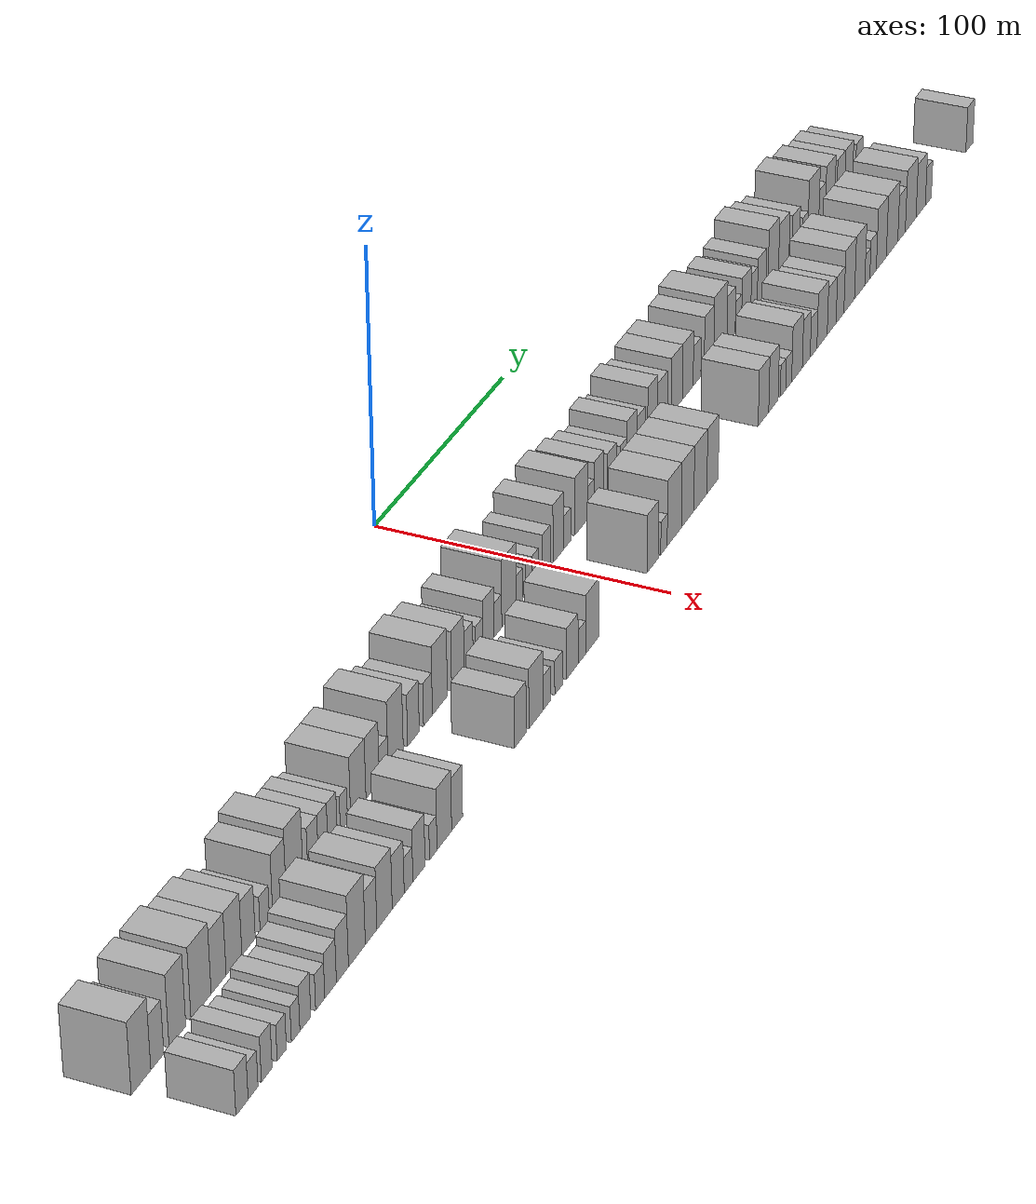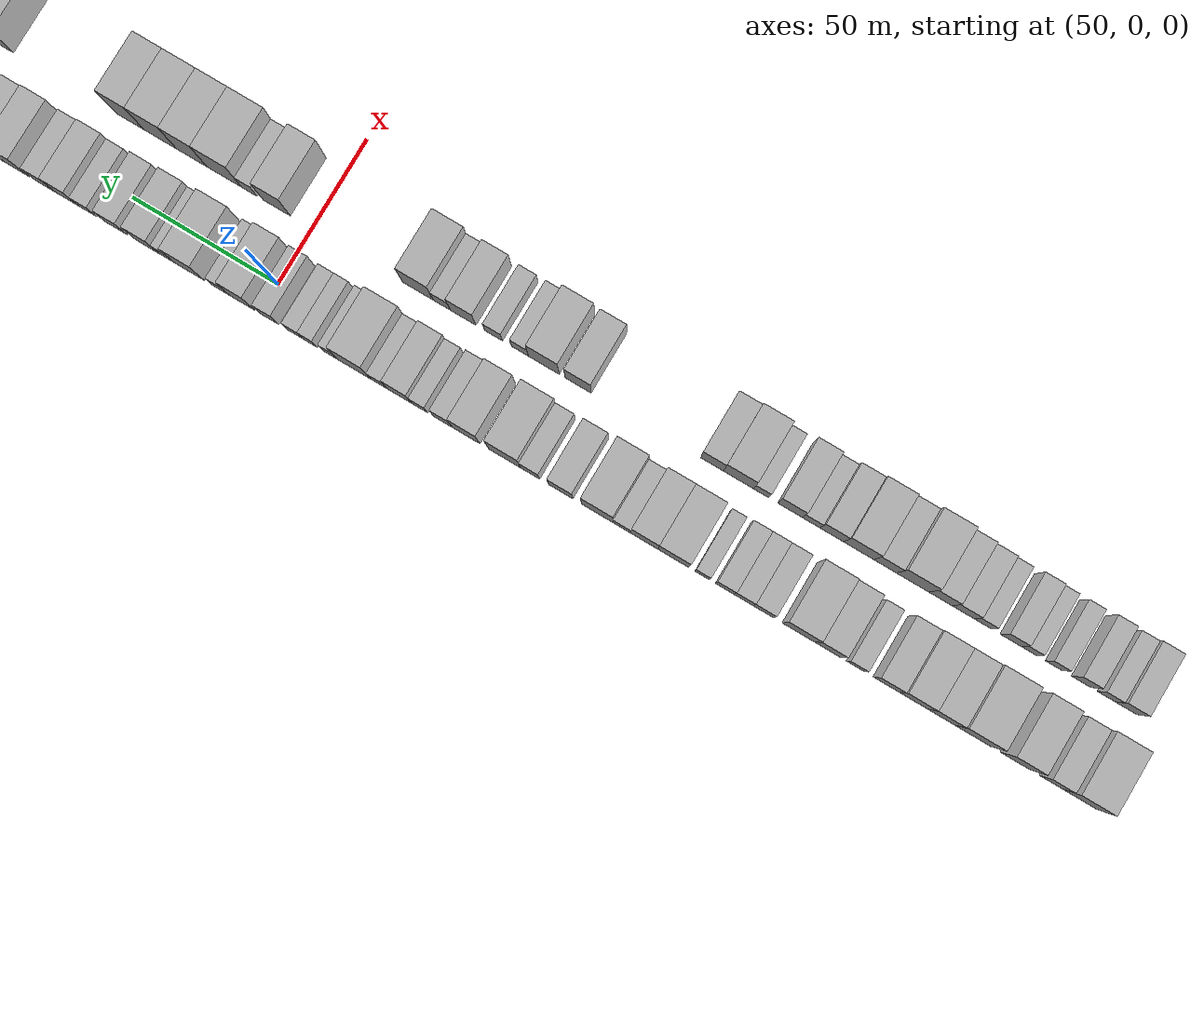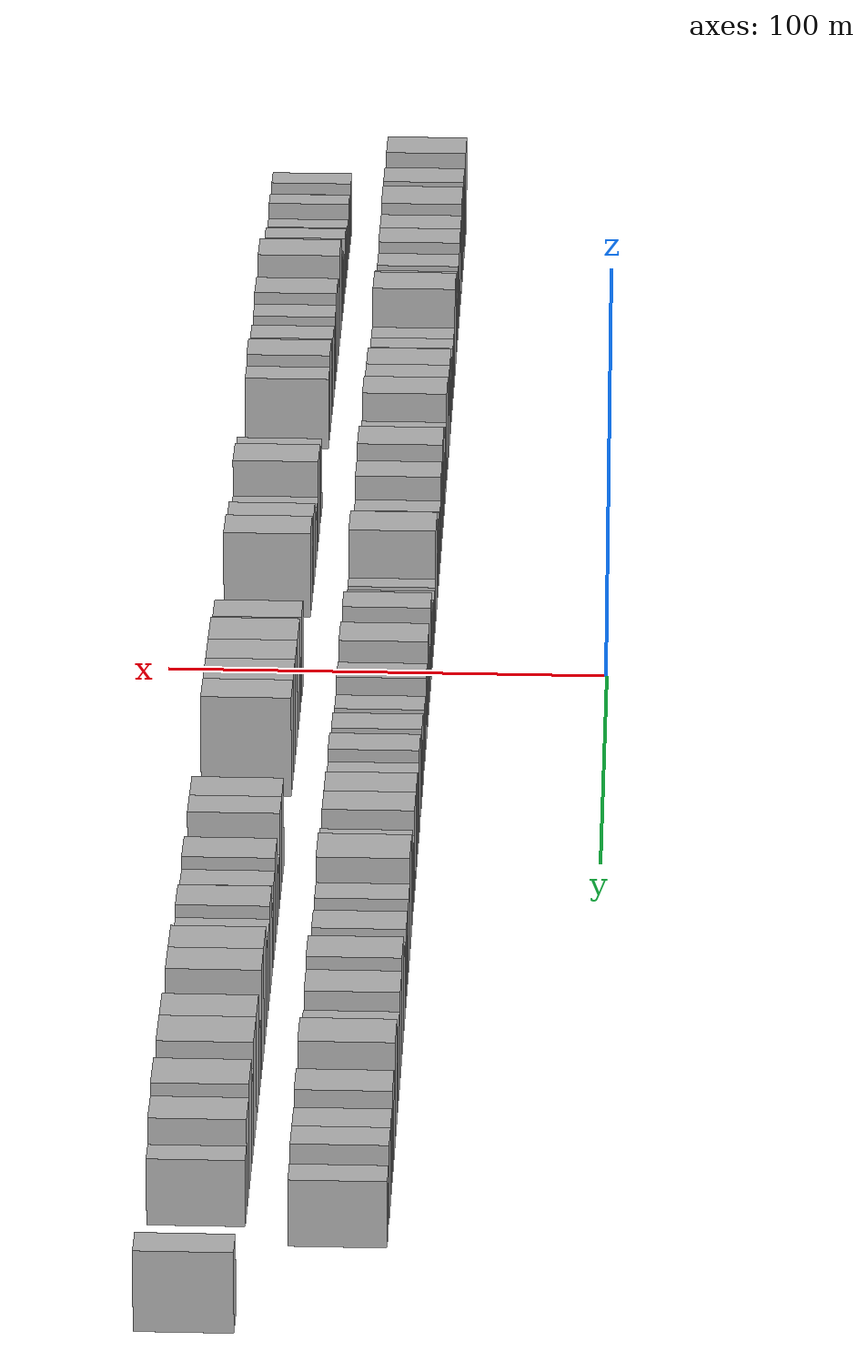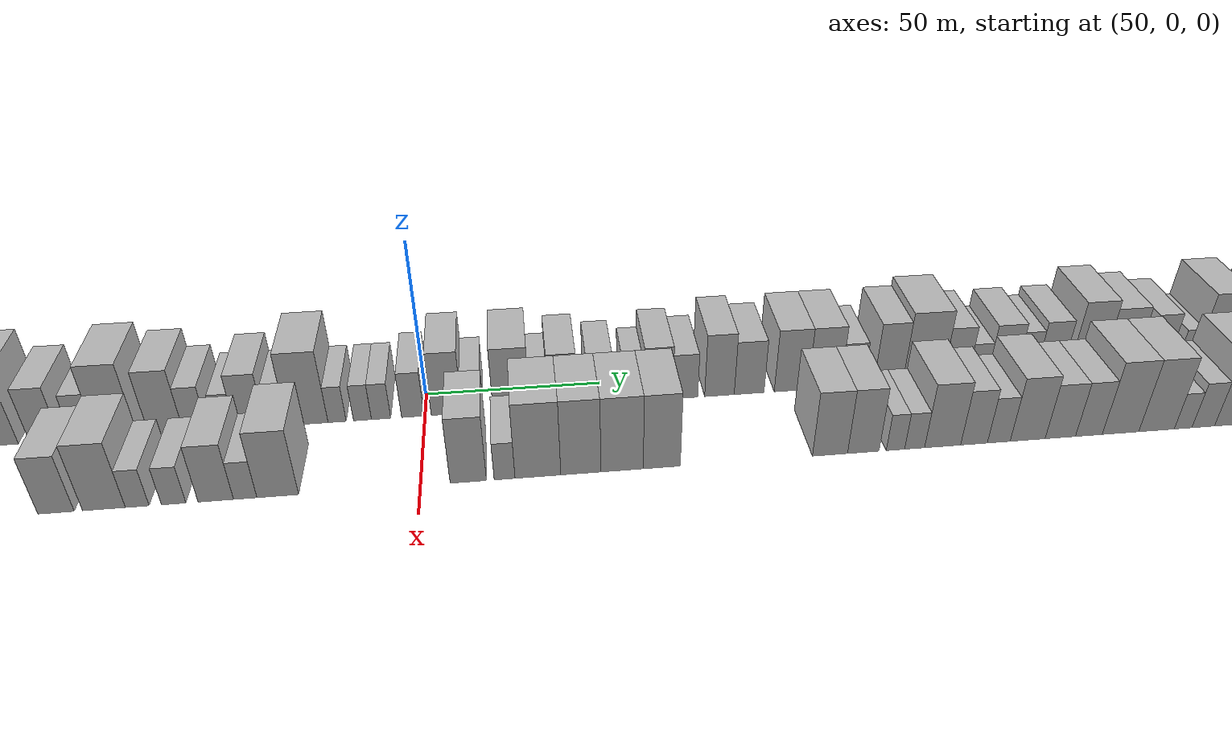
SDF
<sdf version="1.6">
 <world name="default">
  <scene>
   <sky><clouds><speed>12</speed></clouds></sky>
   <ambient>0.4 0.4 0.4 1</ambient>
   <background>0.7 0.7 0.7 1</background>
   <shadows>1</shadows>
  </scene>
  <gravity>0 0 -9.8066</gravity>
  <magnetic_field>6e-06 2.3e-05 -4.2e-05</magnetic_field>
  <physics default="0" name="default_physics" type="ode">
   <ode>
    <solver>
     <type>quick</type>
     <iters>10</iters>
     <sor>1.0</sor>
     <use_dynamic_moi_rescaling>0</use_dynamic_moi_rescaling>
    </solver>
    <constraints>
     <cfm>0</cfm>
     <erp>0.2</erp>
     <contact_max_correcting_vel>100</contact_max_correcting_vel>
     <contact_surface_layer>0.001</contact_surface_layer>
    </constraints>
   </ode>
   <max_step_size>0.004</max_step_size>
   <real_time_factor>1</real_time_factor>
   <real_time_update_rate>250</real_time_update_rate>
  </physics>
  <light name="sun" type="directional">
   <pose>0 0 10 0 0 0</pose>
   <diffuse>0.8 0.8 0.8 1</diffuse>
   <specular>0.2 0.2 0.2 1</specular>
   <attenuation>
    <range>1000</range>
    <constant>0.9</constant>
    <linear>0.01</linear>
    <quadratic>0.001</quadratic>
   </attenuation>
   <direction>-0.5 0.1 -0.9</direction>
  </light>
  <model name="building_1">
   <static>1</static>
   <pose>50.0000 -272.4580 0 0.000000 0.000000 0.000000</pose>
   <link name="link">
    <pose>0 0 12.00 0 0 0</pose>
    <collision name="collision"><geometry><box><size>20.0000 11.0839 24.0000</size></box></geometry></collision>
    <visual name="visual">
     <cast_shadows>0</cast_shadows>
     <geometry><box><size>20.0000 11.0839 24.0000</size></box></geometry>
     <material>
      <script>
       <uri>model://HANNAS_wall/materials/scripts</uri>
       <uri>model://HANNAS_wall/materials/textures</uri>
       <name>vrc/HANNAS_wall</name>
      </script>
     </material>
    </visual>
   </link>
  </model>
  <model name="building_2">
   <static>1</static>
   <pose>50.0000 -263.2071 0 0.000000 0.000000 0.000000</pose>
   <link name="link">
    <pose>0 0 9.00 0 0 0</pose>
    <collision name="collision"><geometry><box><size>20.0000 7.4179 18.0000</size></box></geometry></collision>
    <visual name="visual">
     <cast_shadows>0</cast_shadows>
     <geometry><box><size>20.0000 7.4179 18.0000</size></box></geometry>
     <material>
      <script>
       <uri>model://HANNAS_wall/materials/scripts</uri>
       <uri>model://HANNAS_wall/materials/textures</uri>
       <name>vrc/HANNAS_wall</name>
      </script>
     </material>
    </visual>
   </link>
  </model>
  <model name="building_3">
   <static>1</static>
   <pose>50.0000 -251.6406 0 0.000000 0.000000 0.000000</pose>
   <link name="link">
    <pose>0 0 12.00 0 0 0</pose>
    <collision name="collision"><geometry><box><size>20.0000 9.7152 24.0000</size></box></geometry></collision>
    <visual name="visual">
     <cast_shadows>0</cast_shadows>
     <geometry><box><size>20.0000 9.7152 24.0000</size></box></geometry>
     <material>
      <script>
       <uri>model://HANNAS_wall/materials/scripts</uri>
       <uri>model://HANNAS_wall/materials/textures</uri>
       <name>vrc/HANNAS_wall</name>
      </script>
     </material>
    </visual>
   </link>
  </model>
  <model name="building_4">
   <static>1</static>
   <pose>50.0000 -237.8133 0 0.000000 0.000000 0.000000</pose>
   <link name="link">
    <pose>0 0 12.00 0 0 0</pose>
    <collision name="collision"><geometry><box><size>20.0000 11.9394 24.0000</size></box></geometry></collision>
    <visual name="visual">
     <cast_shadows>0</cast_shadows>
     <geometry><box><size>20.0000 11.9394 24.0000</size></box></geometry>
     <material>
      <script>
       <uri>model://HANNAS_wall/materials/scripts</uri>
       <uri>model://HANNAS_wall/materials/textures</uri>
       <name>vrc/HANNAS_wall</name>
      </script>
     </material>
    </visual>
   </link>
  </model>
  <model name="building_5">
   <static>1</static>
   <pose>50.0000 -227.3742 0 0.000000 0.000000 0.000000</pose>
   <link name="link">
    <pose>0 0 10.50 0 0 0</pose>
    <collision name="collision"><geometry><box><size>20.0000 8.9388 21.0000</size></box></geometry></collision>
    <visual name="visual">
     <cast_shadows>0</cast_shadows>
     <geometry><box><size>20.0000 8.9388 21.0000</size></box></geometry>
     <material>
      <script>
       <uri>model://HANNAS_wall/materials/scripts</uri>
       <uri>model://HANNAS_wall/materials/textures</uri>
       <name>vrc/HANNAS_wall</name>
      </script>
     </material>
    </visual>
   </link>
  </model>
  <model name="building_6">
   <static>1</static>
   <pose>50.0000 -218.1332 0 0.000000 0.000000 0.000000</pose>
   <link name="link">
    <pose>0 0 10.50 0 0 0</pose>
    <collision name="collision"><geometry><box><size>20.0000 9.5433 21.0000</size></box></geometry></collision>
    <visual name="visual">
     <cast_shadows>0</cast_shadows>
     <geometry><box><size>20.0000 9.5433 21.0000</size></box></geometry>
     <material>
      <script>
       <uri>model://HANNAS_wall/materials/scripts</uri>
       <uri>model://HANNAS_wall/materials/textures</uri>
       <name>vrc/HANNAS_wall</name>
      </script>
     </material>
    </visual>
   </link>
  </model>
  <model name="building_7">
   <static>1</static>
   <pose>50.0000 -209.2795 0 0.000000 0.000000 0.000000</pose>
   <link name="link">
    <pose>0 0 9.00 0 0 0</pose>
    <collision name="collision"><geometry><box><size>20.0000 8.1641 18.0000</size></box></geometry></collision>
    <visual name="visual">
     <cast_shadows>0</cast_shadows>
     <geometry><box><size>20.0000 8.1641 18.0000</size></box></geometry>
     <material>
      <script>
       <uri>model://HANNAS_wall/materials/scripts</uri>
       <uri>model://HANNAS_wall/materials/textures</uri>
       <name>vrc/HANNAS_wall</name>
      </script>
     </material>
    </visual>
   </link>
  </model>
  <model name="building_8">
   <static>1</static>
   <pose>50.0000 -199.2894 0 0.000000 0.000000 0.000000</pose>
   <link name="link">
    <pose>0 0 6.00 0 0 0</pose>
    <collision name="collision"><geometry><box><size>20.0000 5.8160 12.0000</size></box></geometry></collision>
    <visual name="visual">
     <cast_shadows>0</cast_shadows>
     <geometry><box><size>20.0000 5.8160 12.0000</size></box></geometry>
     <material>
      <script>
       <uri>model://HANNAS_wall/materials/scripts</uri>
       <uri>model://HANNAS_wall/materials/textures</uri>
       <name>vrc/HANNAS_wall</name>
      </script>
     </material>
    </visual>
   </link>
  </model>
  <model name="building_9">
   <static>1</static>
   <pose>50.0000 -190.1511 0 0.000000 0.000000 0.000000</pose>
   <link name="link">
    <pose>0 0 10.50 0 0 0</pose>
    <collision name="collision"><geometry><box><size>20.0000 8.4607 21.0000</size></box></geometry></collision>
    <visual name="visual">
     <cast_shadows>0</cast_shadows>
     <geometry><box><size>20.0000 8.4607 21.0000</size></box></geometry>
     <material>
      <script>
       <uri>model://HANNAS_wall/materials/scripts</uri>
       <uri>model://HANNAS_wall/materials/textures</uri>
       <name>vrc/HANNAS_wall</name>
      </script>
     </material>
    </visual>
   </link>
  </model>
  <model name="building_10">
   <static>1</static>
   <pose>50.0000 -180.5715 0 0.000000 0.000000 0.000000</pose>
   <link name="link">
    <pose>0 0 12.00 0 0 0</pose>
    <collision name="collision"><geometry><box><size>20.0000 10.6986 24.0000</size></box></geometry></collision>
    <visual name="visual">
     <cast_shadows>0</cast_shadows>
     <geometry><box><size>20.0000 10.6986 24.0000</size></box></geometry>
     <material>
      <script>
       <uri>model://HANNAS_wall/materials/scripts</uri>
       <uri>model://HANNAS_wall/materials/textures</uri>
       <name>vrc/HANNAS_wall</name>
      </script>
     </material>
    </visual>
   </link>
  </model>
  <model name="building_11">
   <static>1</static>
   <pose>50.0000 -168.8535 0 0.000000 0.000000 0.000000</pose>
   <link name="link">
    <pose>0 0 7.50 0 0 0</pose>
    <collision name="collision"><geometry><box><size>20.0000 6.7373 15.0000</size></box></geometry></collision>
    <visual name="visual">
     <cast_shadows>0</cast_shadows>
     <geometry><box><size>20.0000 6.7373 15.0000</size></box></geometry>
     <material>
      <script>
       <uri>model://HANNAS_wall/materials/scripts</uri>
       <uri>model://HANNAS_wall/materials/textures</uri>
       <name>vrc/HANNAS_wall</name>
      </script>
     </material>
    </visual>
   </link>
  </model>
  <model name="building_12">
   <static>1</static>
   <pose>50.0000 -162.3870 0 0.000000 0.000000 0.000000</pose>
   <link name="link">
    <pose>0 0 7.50 0 0 0</pose>
    <collision name="collision"><geometry><box><size>20.0000 6.1957 15.0000</size></box></geometry></collision>
    <visual name="visual">
     <cast_shadows>0</cast_shadows>
     <geometry><box><size>20.0000 6.1957 15.0000</size></box></geometry>
     <material>
      <script>
       <uri>model://HANNAS_wall/materials/scripts</uri>
       <uri>model://HANNAS_wall/materials/textures</uri>
       <name>vrc/HANNAS_wall</name>
      </script>
     </material>
    </visual>
   </link>
  </model>
  <model name="building_13">
   <static>1</static>
   <pose>50.0000 -156.2101 0 0.000000 0.000000 0.000000</pose>
   <link name="link">
    <pose>0 0 7.50 0 0 0</pose>
    <collision name="collision"><geometry><box><size>20.0000 6.1582 15.0000</size></box></geometry></collision>
    <visual name="visual">
     <cast_shadows>0</cast_shadows>
     <geometry><box><size>20.0000 6.1582 15.0000</size></box></geometry>
     <material>
      <script>
       <uri>model://HANNAS_wall/materials/scripts</uri>
       <uri>model://HANNAS_wall/materials/textures</uri>
       <name>vrc/HANNAS_wall</name>
      </script>
     </material>
    </visual>
   </link>
  </model>
  <model name="building_14">
   <static>1</static>
   <pose>50.0000 -148.7292 0 0.000000 0.000000 0.000000</pose>
   <link name="link">
    <pose>0 0 6.00 0 0 0</pose>
    <collision name="collision"><geometry><box><size>20.0000 4.8036 12.0000</size></box></geometry></collision>
    <visual name="visual">
     <cast_shadows>0</cast_shadows>
     <geometry><box><size>20.0000 4.8036 12.0000</size></box></geometry>
     <material>
      <script>
       <uri>model://HANNAS_wall/materials/scripts</uri>
       <uri>model://HANNAS_wall/materials/textures</uri>
       <name>vrc/HANNAS_wall</name>
      </script>
     </material>
    </visual>
   </link>
  </model>
  <model name="building_15">
   <static>1</static>
   <pose>50.0000 -139.2050 0 0.000000 0.000000 0.000000</pose>
   <link name="link">
    <pose>0 0 10.50 0 0 0</pose>
    <collision name="collision"><geometry><box><size>20.0000 10.2449 21.0000</size></box></geometry></collision>
    <visual name="visual">
     <cast_shadows>0</cast_shadows>
     <geometry><box><size>20.0000 10.2449 21.0000</size></box></geometry>
     <material>
      <script>
       <uri>model://HANNAS_wall/materials/scripts</uri>
       <uri>model://HANNAS_wall/materials/textures</uri>
       <name>vrc/HANNAS_wall</name>
      </script>
     </material>
    </visual>
   </link>
  </model>
  <model name="building_16">
   <static>1</static>
   <pose>50.0000 -129.5559 0 0.000000 0.000000 0.000000</pose>
   <link name="link">
    <pose>0 0 10.50 0 0 0</pose>
    <collision name="collision"><geometry><box><size>20.0000 9.0533 21.0000</size></box></geometry></collision>
    <visual name="visual">
     <cast_shadows>0</cast_shadows>
     <geometry><box><size>20.0000 9.0533 21.0000</size></box></geometry>
     <material>
      <script>
       <uri>model://HANNAS_wall/materials/scripts</uri>
       <uri>model://HANNAS_wall/materials/textures</uri>
       <name>vrc/HANNAS_wall</name>
      </script>
     </material>
    </visual>
   </link>
  </model>
  <model name="building_17">
   <static>1</static>
   <pose>50.0000 -122.0449 0 0.000000 0.000000 0.000000</pose>
   <link name="link">
    <pose>0 0 6.00 0 0 0</pose>
    <collision name="collision"><geometry><box><size>20.0000 5.9686 12.0000</size></box></geometry></collision>
    <visual name="visual">
     <cast_shadows>0</cast_shadows>
     <geometry><box><size>20.0000 5.9686 12.0000</size></box></geometry>
     <material>
      <script>
       <uri>model://HANNAS_wall/materials/scripts</uri>
       <uri>model://HANNAS_wall/materials/textures</uri>
       <name>vrc/HANNAS_wall</name>
      </script>
     </material>
    </visual>
   </link>
  </model>
  <model name="building_18">
   <static>1</static>
   <pose>50.0000 -113.8500 0 0.000000 0.000000 0.000000</pose>
   <link name="link">
    <pose>0 0 12.00 0 0 0</pose>
    <collision name="collision"><geometry><box><size>20.0000 10.4212 24.0000</size></box></geometry></collision>
    <visual name="visual">
     <cast_shadows>0</cast_shadows>
     <geometry><box><size>20.0000 10.4212 24.0000</size></box></geometry>
     <material>
      <script>
       <uri>model://HANNAS_wall/materials/scripts</uri>
       <uri>model://HANNAS_wall/materials/textures</uri>
       <name>vrc/HANNAS_wall</name>
      </script>
     </material>
    </visual>
   </link>
  </model>
  <model name="building_19">
   <static>1</static>
   <pose>50.0000 -101.5879 0 0.000000 0.000000 0.000000</pose>
   <link name="link">
    <pose>0 0 9.00 0 0 0</pose>
    <collision name="collision"><geometry><box><size>20.0000 8.1029 18.0000</size></box></geometry></collision>
    <visual name="visual">
     <cast_shadows>0</cast_shadows>
     <geometry><box><size>20.0000 8.1029 18.0000</size></box></geometry>
     <material>
      <script>
       <uri>model://HANNAS_wall/materials/scripts</uri>
       <uri>model://HANNAS_wall/materials/textures</uri>
       <name>vrc/HANNAS_wall</name>
      </script>
     </material>
    </visual>
   </link>
  </model>
  <model name="building_20">
   <static>1</static>
   <pose>50.0000 -91.3871 0 0.000000 0.000000 0.000000</pose>
   <link name="link">
    <pose>0 0 7.50 0 0 0</pose>
    <collision name="collision"><geometry><box><size>20.0000 6.2987 15.0000</size></box></geometry></collision>
    <visual name="visual">
     <cast_shadows>0</cast_shadows>
     <geometry><box><size>20.0000 6.2987 15.0000</size></box></geometry>
     <material>
      <script>
       <uri>model://HANNAS_wall/materials/scripts</uri>
       <uri>model://HANNAS_wall/materials/textures</uri>
       <name>vrc/HANNAS_wall</name>
      </script>
     </material>
    </visual>
   </link>
  </model>
  <model name="building_21">
   <static>1</static>
   <pose>50.0000 -82.8770 0 0.000000 0.000000 0.000000</pose>
   <link name="link">
    <pose>0 0 12.00 0 0 0</pose>
    <collision name="collision"><geometry><box><size>20.0000 10.7214 24.0000</size></box></geometry></collision>
    <visual name="visual">
     <cast_shadows>0</cast_shadows>
     <geometry><box><size>20.0000 10.7214 24.0000</size></box></geometry>
     <material>
      <script>
       <uri>model://HANNAS_wall/materials/scripts</uri>
       <uri>model://HANNAS_wall/materials/textures</uri>
       <name>vrc/HANNAS_wall</name>
      </script>
     </material>
    </visual>
   </link>
  </model>
  <model name="building_22">
   <static>1</static>
   <pose>50.0000 -69.9177 0 0.000000 0.000000 0.000000</pose>
   <link name="link">
    <pose>0 0 10.50 0 0 0</pose>
    <collision name="collision"><geometry><box><size>20.0000 9.1972 21.0000</size></box></geometry></collision>
    <visual name="visual">
     <cast_shadows>0</cast_shadows>
     <geometry><box><size>20.0000 9.1972 21.0000</size></box></geometry>
     <material>
      <script>
       <uri>model://HANNAS_wall/materials/scripts</uri>
       <uri>model://HANNAS_wall/materials/textures</uri>
       <name>vrc/HANNAS_wall</name>
      </script>
     </material>
    </visual>
   </link>
  </model>
  <model name="building_23">
   <static>1</static>
   <pose>50.0000 -62.0917 0 0.000000 0.000000 0.000000</pose>
   <link name="link">
    <pose>0 0 7.50 0 0 0</pose>
    <collision name="collision"><geometry><box><size>20.0000 6.4550 15.0000</size></box></geometry></collision>
    <visual name="visual">
     <cast_shadows>0</cast_shadows>
     <geometry><box><size>20.0000 6.4550 15.0000</size></box></geometry>
     <material>
      <script>
       <uri>model://HANNAS_wall/materials/scripts</uri>
       <uri>model://HANNAS_wall/materials/textures</uri>
       <name>vrc/HANNAS_wall</name>
      </script>
     </material>
    </visual>
   </link>
  </model>
  <model name="building_24">
   <static>1</static>
   <pose>50.0000 -54.2108 0 0.000000 0.000000 0.000000</pose>
   <link name="link">
    <pose>0 0 6.00 0 0 0</pose>
    <collision name="collision"><geometry><box><size>20.0000 5.3067 12.0000</size></box></geometry></collision>
    <visual name="visual">
     <cast_shadows>0</cast_shadows>
     <geometry><box><size>20.0000 5.3067 12.0000</size></box></geometry>
     <material>
      <script>
       <uri>model://HANNAS_wall/materials/scripts</uri>
       <uri>model://HANNAS_wall/materials/textures</uri>
       <name>vrc/HANNAS_wall</name>
      </script>
     </material>
    </visual>
   </link>
  </model>
  <model name="building_25">
   <static>1</static>
   <pose>50.0000 -47.4752 0 0.000000 0.000000 0.000000</pose>
   <link name="link">
    <pose>0 0 9.00 0 0 0</pose>
    <collision name="collision"><geometry><box><size>20.0000 8.1644 18.0000</size></box></geometry></collision>
    <visual name="visual">
     <cast_shadows>0</cast_shadows>
     <geometry><box><size>20.0000 8.1644 18.0000</size></box></geometry>
     <material>
      <script>
       <uri>model://HANNAS_wall/materials/scripts</uri>
       <uri>model://HANNAS_wall/materials/textures</uri>
       <name>vrc/HANNAS_wall</name>
      </script>
     </material>
    </visual>
   </link>
  </model>
  <model name="building_26">
   <static>1</static>
   <pose>50.0000 -40.4975 0 0.000000 0.000000 0.000000</pose>
   <link name="link">
    <pose>0 0 6.00 0 0 0</pose>
    <collision name="collision"><geometry><box><size>20.0000 5.7911 12.0000</size></box></geometry></collision>
    <visual name="visual">
     <cast_shadows>0</cast_shadows>
     <geometry><box><size>20.0000 5.7911 12.0000</size></box></geometry>
     <material>
      <script>
       <uri>model://HANNAS_wall/materials/scripts</uri>
       <uri>model://HANNAS_wall/materials/textures</uri>
       <name>vrc/HANNAS_wall</name>
      </script>
     </material>
    </visual>
   </link>
  </model>
  <model name="building_27">
   <static>1</static>
   <pose>50.0000 -32.0658 0 0.000000 0.000000 0.000000</pose>
   <link name="link">
    <pose>0 0 12.00 0 0 0</pose>
    <collision name="collision"><geometry><box><size>20.0000 11.0724 24.0000</size></box></geometry></collision>
    <visual name="visual">
     <cast_shadows>0</cast_shadows>
     <geometry><box><size>20.0000 11.0724 24.0000</size></box></geometry>
     <material>
      <script>
       <uri>model://HANNAS_wall/materials/scripts</uri>
       <uri>model://HANNAS_wall/materials/textures</uri>
       <name>vrc/HANNAS_wall</name>
      </script>
     </material>
    </visual>
   </link>
  </model>
  <model name="building_28">
   <static>1</static>
   <pose>50.0000 -24.0606 0 0.000000 0.000000 0.000000</pose>
   <link name="link">
    <pose>0 0 6.00 0 0 0</pose>
    <collision name="collision"><geometry><box><size>20.0000 4.9379 12.0000</size></box></geometry></collision>
    <visual name="visual">
     <cast_shadows>0</cast_shadows>
     <geometry><box><size>20.0000 4.9379 12.0000</size></box></geometry>
     <material>
      <script>
       <uri>model://HANNAS_wall/materials/scripts</uri>
       <uri>model://HANNAS_wall/materials/textures</uri>
       <name>vrc/HANNAS_wall</name>
      </script>
     </material>
    </visual>
   </link>
  </model>
  <model name="building_29">
   <static>1</static>
   <pose>50.0000 -17.1362 0 0.000000 0.000000 0.000000</pose>
   <link name="link">
    <pose>0 0 6.00 0 0 0</pose>
    <collision name="collision"><geometry><box><size>20.0000 4.9109 12.0000</size></box></geometry></collision>
    <visual name="visual">
     <cast_shadows>0</cast_shadows>
     <geometry><box><size>20.0000 4.9109 12.0000</size></box></geometry>
     <material>
      <script>
       <uri>model://HANNAS_wall/materials/scripts</uri>
       <uri>model://HANNAS_wall/materials/textures</uri>
       <name>vrc/HANNAS_wall</name>
      </script>
     </material>
    </visual>
   </link>
  </model>
  <model name="building_30">
   <static>1</static>
   <pose>50.0000 -12.0396 0 0.000000 0.000000 0.000000</pose>
   <link name="link">
    <pose>0 0 6.00 0 0 0</pose>
    <collision name="collision"><geometry><box><size>20.0000 5.2822 12.0000</size></box></geometry></collision>
    <visual name="visual">
     <cast_shadows>0</cast_shadows>
     <geometry><box><size>20.0000 5.2822 12.0000</size></box></geometry>
     <material>
      <script>
       <uri>model://HANNAS_wall/materials/scripts</uri>
       <uri>model://HANNAS_wall/materials/textures</uri>
       <name>vrc/HANNAS_wall</name>
      </script>
     </material>
    </visual>
   </link>
  </model>
  <model name="building_31">
   <static>1</static>
   <pose>50.0000 -3.2938 0 0.000000 0.000000 0.000000</pose>
   <link name="link">
    <pose>0 0 7.50 0 0 0</pose>
    <collision name="collision"><geometry><box><size>20.0000 6.2094 15.0000</size></box></geometry></collision>
    <visual name="visual">
     <cast_shadows>0</cast_shadows>
     <geometry><box><size>20.0000 6.2094 15.0000</size></box></geometry>
     <material>
      <script>
       <uri>model://HANNAS_wall/materials/scripts</uri>
       <uri>model://HANNAS_wall/materials/textures</uri>
       <name>vrc/HANNAS_wall</name>
      </script>
     </material>
    </visual>
   </link>
  </model>
  <model name="building_32">
   <static>1</static>
   <pose>50.0000 6.1008 0 0.000000 0.000000 0.000000</pose>
   <link name="link">
    <pose>0 0 10.50 0 0 0</pose>
    <collision name="collision"><geometry><box><size>20.0000 8.5798 21.0000</size></box></geometry></collision>
    <visual name="visual">
     <cast_shadows>0</cast_shadows>
     <geometry><box><size>20.0000 8.5798 21.0000</size></box></geometry>
     <material>
      <script>
       <uri>model://HANNAS_wall/materials/scripts</uri>
       <uri>model://HANNAS_wall/materials/textures</uri>
       <name>vrc/HANNAS_wall</name>
      </script>
     </material>
    </visual>
   </link>
  </model>
  <model name="building_33">
   <static>1</static>
   <pose>50.0000 13.1931 0 0.000000 0.000000 0.000000</pose>
   <link name="link">
    <pose>0 0 6.00 0 0 0</pose>
    <collision name="collision"><geometry><box><size>20.0000 5.6048 12.0000</size></box></geometry></collision>
    <visual name="visual">
     <cast_shadows>0</cast_shadows>
     <geometry><box><size>20.0000 5.6048 12.0000</size></box></geometry>
     <material>
      <script>
       <uri>model://HANNAS_wall/materials/scripts</uri>
       <uri>model://HANNAS_wall/materials/textures</uri>
       <name>vrc/HANNAS_wall</name>
      </script>
     </material>
    </visual>
   </link>
  </model>
  <model name="building_34">
   <static>1</static>
   <pose>50.0000 24.0938 0 0.000000 0.000000 0.000000</pose>
   <link name="link">
    <pose>0 0 10.50 0 0 0</pose>
    <collision name="collision"><geometry><box><size>20.0000 10.1967 21.0000</size></box></geometry></collision>
    <visual name="visual">
     <cast_shadows>0</cast_shadows>
     <geometry><box><size>20.0000 10.1967 21.0000</size></box></geometry>
     <material>
      <script>
       <uri>model://HANNAS_wall/materials/scripts</uri>
       <uri>model://HANNAS_wall/materials/textures</uri>
       <name>vrc/HANNAS_wall</name>
      </script>
     </material>
    </visual>
   </link>
  </model>
  <model name="building_35">
   <static>1</static>
   <pose>50.0000 31.8113 0 0.000000 0.000000 0.000000</pose>
   <link name="link">
    <pose>0 0 6.00 0 0 0</pose>
    <collision name="collision"><geometry><box><size>20.0000 5.2383 12.0000</size></box></geometry></collision>
    <visual name="visual">
     <cast_shadows>0</cast_shadows>
     <geometry><box><size>20.0000 5.2383 12.0000</size></box></geometry>
     <material>
      <script>
       <uri>model://HANNAS_wall/materials/scripts</uri>
       <uri>model://HANNAS_wall/materials/textures</uri>
       <name>vrc/HANNAS_wall</name>
      </script>
     </material>
    </visual>
   </link>
  </model>
  <model name="building_36">
   <static>1</static>
   <pose>50.0000 38.5017 0 0.000000 0.000000 0.000000</pose>
   <link name="link">
    <pose>0 0 9.00 0 0 0</pose>
    <collision name="collision"><geometry><box><size>20.0000 8.1425 18.0000</size></box></geometry></collision>
    <visual name="visual">
     <cast_shadows>0</cast_shadows>
     <geometry><box><size>20.0000 8.1425 18.0000</size></box></geometry>
     <material>
      <script>
       <uri>model://HANNAS_wall/materials/scripts</uri>
       <uri>model://HANNAS_wall/materials/textures</uri>
       <name>vrc/HANNAS_wall</name>
      </script>
     </material>
    </visual>
   </link>
  </model>
  <model name="building_37">
   <static>1</static>
   <pose>50.0000 49.2781 0 0.000000 0.000000 0.000000</pose>
   <link name="link">
    <pose>0 0 7.50 0 0 0</pose>
    <collision name="collision"><geometry><box><size>20.0000 7.4103 15.0000</size></box></geometry></collision>
    <visual name="visual">
     <cast_shadows>0</cast_shadows>
     <geometry><box><size>20.0000 7.4103 15.0000</size></box></geometry>
     <material>
      <script>
       <uri>model://HANNAS_wall/materials/scripts</uri>
       <uri>model://HANNAS_wall/materials/textures</uri>
       <name>vrc/HANNAS_wall</name>
      </script>
     </material>
    </visual>
   </link>
  </model>
  <model name="building_38">
   <static>1</static>
   <pose>50.0000 58.9026 0 0.000000 0.000000 0.000000</pose>
   <link name="link">
    <pose>0 0 6.00 0 0 0</pose>
    <collision name="collision"><geometry><box><size>20.0000 5.8385 12.0000</size></box></geometry></collision>
    <visual name="visual">
     <cast_shadows>0</cast_shadows>
     <geometry><box><size>20.0000 5.8385 12.0000</size></box></geometry>
     <material>
      <script>
       <uri>model://HANNAS_wall/materials/scripts</uri>
       <uri>model://HANNAS_wall/materials/textures</uri>
       <name>vrc/HANNAS_wall</name>
      </script>
     </material>
    </visual>
   </link>
  </model>
  <model name="building_39">
   <static>1</static>
   <pose>50.0000 65.9199 0 0.000000 0.000000 0.000000</pose>
   <link name="link">
    <pose>0 0 9.00 0 0 0</pose>
    <collision name="collision"><geometry><box><size>20.0000 8.1960 18.0000</size></box></geometry></collision>
    <visual name="visual">
     <cast_shadows>0</cast_shadows>
     <geometry><box><size>20.0000 8.1960 18.0000</size></box></geometry>
     <material>
      <script>
       <uri>model://HANNAS_wall/materials/scripts</uri>
       <uri>model://HANNAS_wall/materials/textures</uri>
       <name>vrc/HANNAS_wall</name>
      </script>
     </material>
    </visual>
   </link>
  </model>
  <model name="building_40">
   <static>1</static>
   <pose>50.0000 73.6145 0 0.000000 0.000000 0.000000</pose>
   <link name="link">
    <pose>0 0 7.50 0 0 0</pose>
    <collision name="collision"><geometry><box><size>20.0000 7.1932 15.0000</size></box></geometry></collision>
    <visual name="visual">
     <cast_shadows>0</cast_shadows>
     <geometry><box><size>20.0000 7.1932 15.0000</size></box></geometry>
     <material>
      <script>
       <uri>model://HANNAS_wall/materials/scripts</uri>
       <uri>model://HANNAS_wall/materials/textures</uri>
       <name>vrc/HANNAS_wall</name>
      </script>
     </material>
    </visual>
   </link>
  </model>
  <model name="building_41">
   <static>1</static>
   <pose>50.0000 83.5099 0 0.000000 0.000000 0.000000</pose>
   <link name="link">
    <pose>0 0 10.50 0 0 0</pose>
    <collision name="collision"><geometry><box><size>20.0000 8.5977 21.0000</size></box></geometry></collision>
    <visual name="visual">
     <cast_shadows>0</cast_shadows>
     <geometry><box><size>20.0000 8.5977 21.0000</size></box></geometry>
     <material>
      <script>
       <uri>model://HANNAS_wall/materials/scripts</uri>
       <uri>model://HANNAS_wall/materials/textures</uri>
       <name>vrc/HANNAS_wall</name>
      </script>
     </material>
    </visual>
   </link>
  </model>
  <model name="building_42">
   <static>1</static>
   <pose>50.0000 92.1549 0 0.000000 0.000000 0.000000</pose>
   <link name="link">
    <pose>0 0 9.00 0 0 0</pose>
    <collision name="collision"><geometry><box><size>20.0000 8.6923 18.0000</size></box></geometry></collision>
    <visual name="visual">
     <cast_shadows>0</cast_shadows>
     <geometry><box><size>20.0000 8.6923 18.0000</size></box></geometry>
     <material>
      <script>
       <uri>model://HANNAS_wall/materials/scripts</uri>
       <uri>model://HANNAS_wall/materials/textures</uri>
       <name>vrc/HANNAS_wall</name>
      </script>
     </material>
    </visual>
   </link>
  </model>
  <model name="building_43">
   <static>1</static>
   <pose>50.0000 104.4483 0 0.000000 0.000000 0.000000</pose>
   <link name="link">
    <pose>0 0 10.50 0 0 0</pose>
    <collision name="collision"><geometry><box><size>20.0000 9.8944 21.0000</size></box></geometry></collision>
    <visual name="visual">
     <cast_shadows>0</cast_shadows>
     <geometry><box><size>20.0000 9.8944 21.0000</size></box></geometry>
     <material>
      <script>
       <uri>model://HANNAS_wall/materials/scripts</uri>
       <uri>model://HANNAS_wall/materials/textures</uri>
       <name>vrc/HANNAS_wall</name>
      </script>
     </material>
    </visual>
   </link>
  </model>
  <model name="building_44">
   <static>1</static>
   <pose>50.0000 114.1976 0 0.000000 0.000000 0.000000</pose>
   <link name="link">
    <pose>0 0 10.50 0 0 0</pose>
    <collision name="collision"><geometry><box><size>20.0000 9.6041 21.0000</size></box></geometry></collision>
    <visual name="visual">
     <cast_shadows>0</cast_shadows>
     <geometry><box><size>20.0000 9.6041 21.0000</size></box></geometry>
     <material>
      <script>
       <uri>model://HANNAS_wall/materials/scripts</uri>
       <uri>model://HANNAS_wall/materials/textures</uri>
       <name>vrc/HANNAS_wall</name>
      </script>
     </material>
    </visual>
   </link>
  </model>
  <model name="building_45">
   <static>1</static>
   <pose>50.0000 122.4412 0 0.000000 0.000000 0.000000</pose>
   <link name="link">
    <pose>0 0 7.50 0 0 0</pose>
    <collision name="collision"><geometry><box><size>20.0000 6.8831 15.0000</size></box></geometry></collision>
    <visual name="visual">
     <cast_shadows>0</cast_shadows>
     <geometry><box><size>20.0000 6.8831 15.0000</size></box></geometry>
     <material>
      <script>
       <uri>model://HANNAS_wall/materials/scripts</uri>
       <uri>model://HANNAS_wall/materials/textures</uri>
       <name>vrc/HANNAS_wall</name>
      </script>
     </material>
    </visual>
   </link>
  </model>
  <model name="building_46">
   <static>1</static>
   <pose>50.0000 133.2129 0 0.000000 0.000000 0.000000</pose>
   <link name="link">
    <pose>0 0 10.50 0 0 0</pose>
    <collision name="collision"><geometry><box><size>20.0000 8.6603 21.0000</size></box></geometry></collision>
    <visual name="visual">
     <cast_shadows>0</cast_shadows>
     <geometry><box><size>20.0000 8.6603 21.0000</size></box></geometry>
     <material>
      <script>
       <uri>model://HANNAS_wall/materials/scripts</uri>
       <uri>model://HANNAS_wall/materials/textures</uri>
       <name>vrc/HANNAS_wall</name>
      </script>
     </material>
    </visual>
   </link>
  </model>
  <model name="building_47">
   <static>1</static>
   <pose>50.0000 143.5383 0 0.000000 0.000000 0.000000</pose>
   <link name="link">
    <pose>0 0 12.00 0 0 0</pose>
    <collision name="collision"><geometry><box><size>20.0000 11.9904 24.0000</size></box></geometry></collision>
    <visual name="visual">
     <cast_shadows>0</cast_shadows>
     <geometry><box><size>20.0000 11.9904 24.0000</size></box></geometry>
     <material>
      <script>
       <uri>model://HANNAS_wall/materials/scripts</uri>
       <uri>model://HANNAS_wall/materials/textures</uri>
       <name>vrc/HANNAS_wall</name>
      </script>
     </material>
    </visual>
   </link>
  </model>
  <model name="building_48">
   <static>1</static>
   <pose>50.0000 153.3709 0 0.000000 0.000000 0.000000</pose>
   <link name="link">
    <pose>0 0 9.00 0 0 0</pose>
    <collision name="collision"><geometry><box><size>20.0000 7.6747 18.0000</size></box></geometry></collision>
    <visual name="visual">
     <cast_shadows>0</cast_shadows>
     <geometry><box><size>20.0000 7.6747 18.0000</size></box></geometry>
     <material>
      <script>
       <uri>model://HANNAS_wall/materials/scripts</uri>
       <uri>model://HANNAS_wall/materials/textures</uri>
       <name>vrc/HANNAS_wall</name>
      </script>
     </material>
    </visual>
   </link>
  </model>
  <model name="building_49">
   <static>1</static>
   <pose>50.0000 160.1628 0 0.000000 0.000000 0.000000</pose>
   <link name="link">
    <pose>0 0 6.00 0 0 0</pose>
    <collision name="collision"><geometry><box><size>20.0000 5.9092 12.0000</size></box></geometry></collision>
    <visual name="visual">
     <cast_shadows>0</cast_shadows>
     <geometry><box><size>20.0000 5.9092 12.0000</size></box></geometry>
     <material>
      <script>
       <uri>model://HANNAS_wall/materials/scripts</uri>
       <uri>model://HANNAS_wall/materials/textures</uri>
       <name>vrc/HANNAS_wall</name>
      </script>
     </material>
    </visual>
   </link>
  </model>
  <model name="building_50">
   <static>1</static>
   <pose>50.0000 167.4937 0 0.000000 0.000000 0.000000</pose>
   <link name="link">
    <pose>0 0 9.00 0 0 0</pose>
    <collision name="collision"><geometry><box><size>20.0000 8.7525 18.0000</size></box></geometry></collision>
    <visual name="visual">
     <cast_shadows>0</cast_shadows>
     <geometry><box><size>20.0000 8.7525 18.0000</size></box></geometry>
     <material>
      <script>
       <uri>model://HANNAS_wall/materials/scripts</uri>
       <uri>model://HANNAS_wall/materials/textures</uri>
       <name>vrc/HANNAS_wall</name>
      </script>
     </material>
    </visual>
   </link>
  </model>
  <model name="building_51">
   <static>1</static>
   <pose>50.0000 174.8730 0 0.000000 0.000000 0.000000</pose>
   <link name="link">
    <pose>0 0 7.50 0 0 0</pose>
    <collision name="collision"><geometry><box><size>20.0000 6.0060 15.0000</size></box></geometry></collision>
    <visual name="visual">
     <cast_shadows>0</cast_shadows>
     <geometry><box><size>20.0000 6.0060 15.0000</size></box></geometry>
     <material>
      <script>
       <uri>model://HANNAS_wall/materials/scripts</uri>
       <uri>model://HANNAS_wall/materials/textures</uri>
       <name>vrc/HANNAS_wall</name>
      </script>
     </material>
    </visual>
   </link>
  </model>
  <model name="building_52">
   <static>1</static>
   <pose>50.0000 181.9415 0 0.000000 0.000000 0.000000</pose>
   <link name="link">
    <pose>0 0 9.00 0 0 0</pose>
    <collision name="collision"><geometry><box><size>20.0000 8.1310 18.0000</size></box></geometry></collision>
    <visual name="visual">
     <cast_shadows>0</cast_shadows>
     <geometry><box><size>20.0000 8.1310 18.0000</size></box></geometry>
     <material>
      <script>
       <uri>model://HANNAS_wall/materials/scripts</uri>
       <uri>model://HANNAS_wall/materials/textures</uri>
       <name>vrc/HANNAS_wall</name>
      </script>
     </material>
    </visual>
   </link>
  </model>
  <model name="building_53">
   <static>1</static>
   <pose>50.0000 193.0817 0 0.000000 0.000000 0.000000</pose>
   <link name="link">
    <pose>0 0 12.00 0 0 0</pose>
    <collision name="collision"><geometry><box><size>20.0000 10.1494 24.0000</size></box></geometry></collision>
    <visual name="visual">
     <cast_shadows>0</cast_shadows>
     <geometry><box><size>20.0000 10.1494 24.0000</size></box></geometry>
     <material>
      <script>
       <uri>model://HANNAS_wall/materials/scripts</uri>
       <uri>model://HANNAS_wall/materials/textures</uri>
       <name>vrc/HANNAS_wall</name>
      </script>
     </material>
    </visual>
   </link>
  </model>
  <model name="building_54">
   <static>1</static>
   <pose>50.0000 203.2365 0 0.000000 0.000000 0.000000</pose>
   <link name="link">
    <pose>0 0 10.50 0 0 0</pose>
    <collision name="collision"><geometry><box><size>20.0000 10.1603 21.0000</size></box></geometry></collision>
    <visual name="visual">
     <cast_shadows>0</cast_shadows>
     <geometry><box><size>20.0000 10.1603 21.0000</size></box></geometry>
     <material>
      <script>
       <uri>model://HANNAS_wall/materials/scripts</uri>
       <uri>model://HANNAS_wall/materials/textures</uri>
       <name>vrc/HANNAS_wall</name>
      </script>
     </material>
    </visual>
   </link>
  </model>
  <model name="building_55">
   <static>1</static>
   <pose>50.0000 215.0271 0 0.000000 0.000000 0.000000</pose>
   <link name="link">
    <pose>0 0 9.00 0 0 0</pose>
    <collision name="collision"><geometry><box><size>20.0000 7.4208 18.0000</size></box></geometry></collision>
    <visual name="visual">
     <cast_shadows>0</cast_shadows>
     <geometry><box><size>20.0000 7.4208 18.0000</size></box></geometry>
     <material>
      <script>
       <uri>model://HANNAS_wall/materials/scripts</uri>
       <uri>model://HANNAS_wall/materials/textures</uri>
       <name>vrc/HANNAS_wall</name>
      </script>
     </material>
    </visual>
   </link>
  </model>
  <model name="building_56">
   <static>1</static>
   <pose>50.0000 224.3459 0 0.000000 0.000000 0.000000</pose>
   <link name="link">
    <pose>0 0 6.00 0 0 0</pose>
    <collision name="collision"><geometry><box><size>20.0000 5.2167 12.0000</size></box></geometry></collision>
    <visual name="visual">
     <cast_shadows>0</cast_shadows>
     <geometry><box><size>20.0000 5.2167 12.0000</size></box></geometry>
     <material>
      <script>
       <uri>model://HANNAS_wall/materials/scripts</uri>
       <uri>model://HANNAS_wall/materials/textures</uri>
       <name>vrc/HANNAS_wall</name>
      </script>
     </material>
    </visual>
   </link>
  </model>
  <model name="building_57">
   <static>1</static>
   <pose>50.0000 232.4189 0 0.000000 0.000000 0.000000</pose>
   <link name="link">
    <pose>0 0 12.00 0 0 0</pose>
    <collision name="collision"><geometry><box><size>20.0000 10.9293 24.0000</size></box></geometry></collision>
    <visual name="visual">
     <cast_shadows>0</cast_shadows>
     <geometry><box><size>20.0000 10.9293 24.0000</size></box></geometry>
     <material>
      <script>
       <uri>model://HANNAS_wall/materials/scripts</uri>
       <uri>model://HANNAS_wall/materials/textures</uri>
       <name>vrc/HANNAS_wall</name>
      </script>
     </material>
    </visual>
   </link>
  </model>
  <model name="building_58">
   <static>1</static>
   <pose>50.0000 241.2010 0 0.000000 0.000000 0.000000</pose>
   <link name="link">
    <pose>0 0 7.50 0 0 0</pose>
    <collision name="collision"><geometry><box><size>20.0000 6.6349 15.0000</size></box></geometry></collision>
    <visual name="visual">
     <cast_shadows>0</cast_shadows>
     <geometry><box><size>20.0000 6.6349 15.0000</size></box></geometry>
     <material>
      <script>
       <uri>model://HANNAS_wall/materials/scripts</uri>
       <uri>model://HANNAS_wall/materials/textures</uri>
       <name>vrc/HANNAS_wall</name>
      </script>
     </material>
    </visual>
   </link>
  </model>
  <model name="building_59">
   <static>1</static>
   <pose>50.0000 249.2946 0 0.000000 0.000000 0.000000</pose>
   <link name="link">
    <pose>0 0 10.50 0 0 0</pose>
    <collision name="collision"><geometry><box><size>20.0000 9.5523 21.0000</size></box></geometry></collision>
    <visual name="visual">
     <cast_shadows>0</cast_shadows>
     <geometry><box><size>20.0000 9.5523 21.0000</size></box></geometry>
     <material>
      <script>
       <uri>model://HANNAS_wall/materials/scripts</uri>
       <uri>model://HANNAS_wall/materials/textures</uri>
       <name>vrc/HANNAS_wall</name>
      </script>
     </material>
    </visual>
   </link>
  </model>
  <model name="building_60">
   <static>1</static>
   <pose>50.0000 260.2479 0 0.000000 0.000000 0.000000</pose>
   <link name="link">
    <pose>0 0 9.00 0 0 0</pose>
    <collision name="collision"><geometry><box><size>20.0000 8.3544 18.0000</size></box></geometry></collision>
    <visual name="visual">
     <cast_shadows>0</cast_shadows>
     <geometry><box><size>20.0000 8.3544 18.0000</size></box></geometry>
     <material>
      <script>
       <uri>model://HANNAS_wall/materials/scripts</uri>
       <uri>model://HANNAS_wall/materials/textures</uri>
       <name>vrc/HANNAS_wall</name>
      </script>
     </material>
    </visual>
   </link>
  </model>
  <model name="building_61">
   <static>1</static>
   <pose>50.0000 268.4460 0 0.000000 0.000000 0.000000</pose>
   <link name="link">
    <pose>0 0 9.00 0 0 0</pose>
    <collision name="collision"><geometry><box><size>20.0000 8.0417 18.0000</size></box></geometry></collision>
    <visual name="visual">
     <cast_shadows>0</cast_shadows>
     <geometry><box><size>20.0000 8.0417 18.0000</size></box></geometry>
     <material>
      <script>
       <uri>model://HANNAS_wall/materials/scripts</uri>
       <uri>model://HANNAS_wall/materials/textures</uri>
       <name>vrc/HANNAS_wall</name>
      </script>
     </material>
    </visual>
   </link>
  </model>
  <model name="building_62">
   <static>1</static>
   <pose>50.0000 279.0263 0 0.000000 0.000000 0.000000</pose>
   <link name="link">
    <pose>0 0 7.50 0 0 0</pose>
    <collision name="collision"><geometry><box><size>20.0000 7.1189 15.0000</size></box></geometry></collision>
    <visual name="visual">
     <cast_shadows>0</cast_shadows>
     <geometry><box><size>20.0000 7.1189 15.0000</size></box></geometry>
     <material>
      <script>
       <uri>model://HANNAS_wall/materials/scripts</uri>
       <uri>model://HANNAS_wall/materials/textures</uri>
       <name>vrc/HANNAS_wall</name>
      </script>
     </material>
    </visual>
   </link>
  </model>
  <model name="building_63">
   <static>1</static>
   <pose>79.0000 -271.4325 0 0.000000 0.000000 0.000000</pose>
   <link name="link">
    <pose>0 0 7.50 0 0 0</pose>
    <collision name="collision"><geometry><box><size>20.0000 7.1350 15.0000</size></box></geometry></collision>
    <visual name="visual">
     <cast_shadows>0</cast_shadows>
     <geometry><box><size>20.0000 7.1350 15.0000</size></box></geometry>
     <material>
      <script>
       <uri>model://HANNAS_wall/materials/scripts</uri>
       <uri>model://HANNAS_wall/materials/textures</uri>
       <name>vrc/HANNAS_wall</name>
      </script>
     </material>
    </visual>
   </link>
  </model>
  <model name="building_64">
   <static>1</static>
   <pose>79.0000 -264.9563 0 0.000000 0.000000 0.000000</pose>
   <link name="link">
    <pose>0 0 6.00 0 0 0</pose>
    <collision name="collision"><geometry><box><size>20.0000 5.8173 12.0000</size></box></geometry></collision>
    <visual name="visual">
     <cast_shadows>0</cast_shadows>
     <geometry><box><size>20.0000 5.8173 12.0000</size></box></geometry>
     <material>
      <script>
       <uri>model://HANNAS_wall/materials/scripts</uri>
       <uri>model://HANNAS_wall/materials/textures</uri>
       <name>vrc/HANNAS_wall</name>
      </script>
     </material>
    </visual>
   </link>
  </model>
  <model name="building_65">
   <static>1</static>
   <pose>79.0000 -256.8660 0 0.000000 0.000000 0.000000</pose>
   <link name="link">
    <pose>0 0 7.50 0 0 0</pose>
    <collision name="collision"><geometry><box><size>20.0000 6.3634 15.0000</size></box></geometry></collision>
    <visual name="visual">
     <cast_shadows>0</cast_shadows>
     <geometry><box><size>20.0000 6.3634 15.0000</size></box></geometry>
     <material>
      <script>
       <uri>model://HANNAS_wall/materials/scripts</uri>
       <uri>model://HANNAS_wall/materials/textures</uri>
       <name>vrc/HANNAS_wall</name>
      </script>
     </material>
    </visual>
   </link>
  </model>
  <model name="building_66">
   <static>1</static>
   <pose>79.0000 -247.9152 0 0.000000 0.000000 0.000000</pose>
   <link name="link">
    <pose>0 0 6.00 0 0 0</pose>
    <collision name="collision"><geometry><box><size>20.0000 5.5382 12.0000</size></box></geometry></collision>
    <visual name="visual">
     <cast_shadows>0</cast_shadows>
     <geometry><box><size>20.0000 5.5382 12.0000</size></box></geometry>
     <material>
      <script>
       <uri>model://HANNAS_wall/materials/scripts</uri>
       <uri>model://HANNAS_wall/materials/textures</uri>
       <name>vrc/HANNAS_wall</name>
      </script>
     </material>
    </visual>
   </link>
  </model>
  <model name="building_67">
   <static>1</static>
   <pose>79.0000 -239.5707 0 0.000000 0.000000 0.000000</pose>
   <link name="link">
    <pose>0 0 6.00 0 0 0</pose>
    <collision name="collision"><geometry><box><size>20.0000 5.1507 12.0000</size></box></geometry></collision>
    <visual name="visual">
     <cast_shadows>0</cast_shadows>
     <geometry><box><size>20.0000 5.1507 12.0000</size></box></geometry>
     <material>
      <script>
       <uri>model://HANNAS_wall/materials/scripts</uri>
       <uri>model://HANNAS_wall/materials/textures</uri>
       <name>vrc/HANNAS_wall</name>
      </script>
     </material>
    </visual>
   </link>
  </model>
  <model name="building_68">
   <static>1</static>
   <pose>79.0000 -233.6672 0 0.000000 0.000000 0.000000</pose>
   <link name="link">
    <pose>0 0 7.50 0 0 0</pose>
    <collision name="collision"><geometry><box><size>20.0000 6.6565 15.0000</size></box></geometry></collision>
    <visual name="visual">
     <cast_shadows>0</cast_shadows>
     <geometry><box><size>20.0000 6.6565 15.0000</size></box></geometry>
     <material>
      <script>
       <uri>model://HANNAS_wall/materials/scripts</uri>
       <uri>model://HANNAS_wall/materials/textures</uri>
       <name>vrc/HANNAS_wall</name>
      </script>
     </material>
    </visual>
   </link>
  </model>
  <model name="building_69">
   <static>1</static>
   <pose>79.0000 -224.5181 0 0.000000 0.000000 0.000000</pose>
   <link name="link">
    <pose>0 0 6.00 0 0 0</pose>
    <collision name="collision"><geometry><box><size>20.0000 5.6416 12.0000</size></box></geometry></collision>
    <visual name="visual">
     <cast_shadows>0</cast_shadows>
     <geometry><box><size>20.0000 5.6416 12.0000</size></box></geometry>
     <material>
      <script>
       <uri>model://HANNAS_wall/materials/scripts</uri>
       <uri>model://HANNAS_wall/materials/textures</uri>
       <name>vrc/HANNAS_wall</name>
      </script>
     </material>
    </visual>
   </link>
  </model>
  <model name="building_70">
   <static>1</static>
   <pose>79.0000 -218.0711 0 0.000000 0.000000 0.000000</pose>
   <link name="link">
    <pose>0 0 7.50 0 0 0</pose>
    <collision name="collision"><geometry><box><size>20.0000 7.2524 15.0000</size></box></geometry></collision>
    <visual name="visual">
     <cast_shadows>0</cast_shadows>
     <geometry><box><size>20.0000 7.2524 15.0000</size></box></geometry>
     <material>
      <script>
       <uri>model://HANNAS_wall/materials/scripts</uri>
       <uri>model://HANNAS_wall/materials/textures</uri>
       <name>vrc/HANNAS_wall</name>
      </script>
     </material>
    </visual>
   </link>
  </model>
  <model name="building_71">
   <static>1</static>
   <pose>79.0000 -210.6546 0 0.000000 0.000000 0.000000</pose>
   <link name="link">
    <pose>0 0 9.00 0 0 0</pose>
    <collision name="collision"><geometry><box><size>20.0000 7.5807 18.0000</size></box></geometry></collision>
    <visual name="visual">
     <cast_shadows>0</cast_shadows>
     <geometry><box><size>20.0000 7.5807 18.0000</size></box></geometry>
     <material>
      <script>
       <uri>model://HANNAS_wall/materials/scripts</uri>
       <uri>model://HANNAS_wall/materials/textures</uri>
       <name>vrc/HANNAS_wall</name>
      </script>
     </material>
    </visual>
   </link>
  </model>
  <model name="building_72">
   <static>1</static>
   <pose>79.0000 -201.5052 0 0.000000 0.000000 0.000000</pose>
   <link name="link">
    <pose>0 0 12.00 0 0 0</pose>
    <collision name="collision"><geometry><box><size>20.0000 10.7180 24.0000</size></box></geometry></collision>
    <visual name="visual">
     <cast_shadows>0</cast_shadows>
     <geometry><box><size>20.0000 10.7180 24.0000</size></box></geometry>
     <material>
      <script>
       <uri>model://HANNAS_wall/materials/scripts</uri>
       <uri>model://HANNAS_wall/materials/textures</uri>
       <name>vrc/HANNAS_wall</name>
      </script>
     </material>
    </visual>
   </link>
  </model>
  <model name="building_73">
   <static>1</static>
   <pose>79.0000 -192.4243 0 0.000000 0.000000 0.000000</pose>
   <link name="link">
    <pose>0 0 9.00 0 0 0</pose>
    <collision name="collision"><geometry><box><size>20.0000 7.4438 18.0000</size></box></geometry></collision>
    <visual name="visual">
     <cast_shadows>0</cast_shadows>
     <geometry><box><size>20.0000 7.4438 18.0000</size></box></geometry>
     <material>
      <script>
       <uri>model://HANNAS_wall/materials/scripts</uri>
       <uri>model://HANNAS_wall/materials/textures</uri>
       <name>vrc/HANNAS_wall</name>
      </script>
     </material>
    </visual>
   </link>
  </model>
  <model name="building_74">
   <static>1</static>
   <pose>79.0000 -183.7045 0 0.000000 0.000000 0.000000</pose>
   <link name="link">
    <pose>0 0 10.50 0 0 0</pose>
    <collision name="collision"><geometry><box><size>20.0000 9.9958 21.0000</size></box></geometry></collision>
    <visual name="visual">
     <cast_shadows>0</cast_shadows>
     <geometry><box><size>20.0000 9.9958 21.0000</size></box></geometry>
     <material>
      <script>
       <uri>model://HANNAS_wall/materials/scripts</uri>
       <uri>model://HANNAS_wall/materials/textures</uri>
       <name>vrc/HANNAS_wall</name>
      </script>
     </material>
    </visual>
   </link>
  </model>
  <model name="building_75">
   <static>1</static>
   <pose>79.0000 -174.7690 0 0.000000 0.000000 0.000000</pose>
   <link name="link">
    <pose>0 0 9.00 0 0 0</pose>
    <collision name="collision"><geometry><box><size>20.0000 7.8751 18.0000</size></box></geometry></collision>
    <visual name="visual">
     <cast_shadows>0</cast_shadows>
     <geometry><box><size>20.0000 7.8751 18.0000</size></box></geometry>
     <material>
      <script>
       <uri>model://HANNAS_wall/materials/scripts</uri>
       <uri>model://HANNAS_wall/materials/textures</uri>
       <name>vrc/HANNAS_wall</name>
      </script>
     </material>
    </visual>
   </link>
  </model>
  <model name="building_76">
   <static>1</static>
   <pose>79.0000 -167.9381 0 0.000000 0.000000 0.000000</pose>
   <link name="link">
    <pose>0 0 6.00 0 0 0</pose>
    <collision name="collision"><geometry><box><size>20.0000 5.7867 12.0000</size></box></geometry></collision>
    <visual name="visual">
     <cast_shadows>0</cast_shadows>
     <geometry><box><size>20.0000 5.7867 12.0000</size></box></geometry>
     <material>
      <script>
       <uri>model://HANNAS_wall/materials/scripts</uri>
       <uri>model://HANNAS_wall/materials/textures</uri>
       <name>vrc/HANNAS_wall</name>
      </script>
     </material>
    </visual>
   </link>
  </model>
  <model name="building_77">
   <static>1</static>
   <pose>79.0000 -160.9713 0 0.000000 0.000000 0.000000</pose>
   <link name="link">
    <pose>0 0 9.00 0 0 0</pose>
    <collision name="collision"><geometry><box><size>20.0000 8.1470 18.0000</size></box></geometry></collision>
    <visual name="visual">
     <cast_shadows>0</cast_shadows>
     <geometry><box><size>20.0000 8.1470 18.0000</size></box></geometry>
     <material>
      <script>
       <uri>model://HANNAS_wall/materials/scripts</uri>
       <uri>model://HANNAS_wall/materials/textures</uri>
       <name>vrc/HANNAS_wall</name>
      </script>
     </material>
    </visual>
   </link>
  </model>
  <model name="building_78">
   <static>1</static>
   <pose>79.0000 -151.3480 0 0.000000 0.000000 0.000000</pose>
   <link name="link">
    <pose>0 0 6.00 0 0 0</pose>
    <collision name="collision"><geometry><box><size>20.0000 5.0995 12.0000</size></box></geometry></collision>
    <visual name="visual">
     <cast_shadows>0</cast_shadows>
     <geometry><box><size>20.0000 5.0995 12.0000</size></box></geometry>
     <material>
      <script>
       <uri>model://HANNAS_wall/materials/scripts</uri>
       <uri>model://HANNAS_wall/materials/textures</uri>
       <name>vrc/HANNAS_wall</name>
      </script>
     </material>
    </visual>
   </link>
  </model>
  <model name="building_79">
   <static>1</static>
   <pose>79.0000 -143.7996 0 0.000000 0.000000 0.000000</pose>
   <link name="link">
    <pose>0 0 10.50 0 0 0</pose>
    <collision name="collision"><geometry><box><size>20.0000 9.9974 21.0000</size></box></geometry></collision>
    <visual name="visual">
     <cast_shadows>0</cast_shadows>
     <geometry><box><size>20.0000 9.9974 21.0000</size></box></geometry>
     <material>
      <script>
       <uri>model://HANNAS_wall/materials/scripts</uri>
       <uri>model://HANNAS_wall/materials/textures</uri>
       <name>vrc/HANNAS_wall</name>
      </script>
     </material>
    </visual>
   </link>
  </model>
  <model name="building_80">
   <static>1</static>
   <pose>79.0000 -135.0164 0 0.000000 0.000000 0.000000</pose>
   <link name="link">
    <pose>0 0 9.00 0 0 0</pose>
    <collision name="collision"><geometry><box><size>20.0000 7.5692 18.0000</size></box></geometry></collision>
    <visual name="visual">
     <cast_shadows>0</cast_shadows>
     <geometry><box><size>20.0000 7.5692 18.0000</size></box></geometry>
     <material>
      <script>
       <uri>model://HANNAS_wall/materials/scripts</uri>
       <uri>model://HANNAS_wall/materials/textures</uri>
       <name>vrc/HANNAS_wall</name>
      </script>
     </material>
    </visual>
   </link>
  </model>
  <model name="building_81">
   <static>1</static>
   <pose>79.0000 -90.1417 0 0.000000 0.000000 0.000000</pose>
   <link name="link">
    <pose>0 0 9.00 0 0 0</pose>
    <collision name="collision"><geometry><box><size>20.0000 8.7267 18.0000</size></box></geometry></collision>
    <visual name="visual">
     <cast_shadows>0</cast_shadows>
     <geometry><box><size>20.0000 8.7267 18.0000</size></box></geometry>
     <material>
      <script>
       <uri>model://HANNAS_wall/materials/scripts</uri>
       <uri>model://HANNAS_wall/materials/textures</uri>
       <name>vrc/HANNAS_wall</name>
      </script>
     </material>
    </visual>
   </link>
  </model>
  <model name="building_82">
   <static>1</static>
   <pose>79.0000 -78.5949 0 0.000000 0.000000 0.000000</pose>
   <link name="link">
    <pose>0 0 10.50 0 0 0</pose>
    <collision name="collision"><geometry><box><size>20.0000 10.3667 21.0000</size></box></geometry></collision>
    <visual name="visual">
     <cast_shadows>0</cast_shadows>
     <geometry><box><size>20.0000 10.3667 21.0000</size></box></geometry>
     <material>
      <script>
       <uri>model://HANNAS_wall/materials/scripts</uri>
       <uri>model://HANNAS_wall/materials/textures</uri>
       <name>vrc/HANNAS_wall</name>
      </script>
     </material>
    </visual>
   </link>
  </model>
  <model name="building_83">
   <static>1</static>
   <pose>79.0000 -70.5244 0 0.000000 0.000000 0.000000</pose>
   <link name="link">
    <pose>0 0 6.00 0 0 0</pose>
    <collision name="collision"><geometry><box><size>20.0000 5.7744 12.0000</size></box></geometry></collision>
    <visual name="visual">
     <cast_shadows>0</cast_shadows>
     <geometry><box><size>20.0000 5.7744 12.0000</size></box></geometry>
     <material>
      <script>
       <uri>model://HANNAS_wall/materials/scripts</uri>
       <uri>model://HANNAS_wall/materials/textures</uri>
       <name>vrc/HANNAS_wall</name>
      </script>
     </material>
    </visual>
   </link>
  </model>
  <model name="building_84">
   <static>1</static>
   <pose>79.0000 -61.6505 0 0.000000 0.000000 0.000000</pose>
   <link name="link">
    <pose>0 0 6.00 0 0 0</pose>
    <collision name="collision"><geometry><box><size>20.0000 5.9735 12.0000</size></box></geometry></collision>
    <visual name="visual">
     <cast_shadows>0</cast_shadows>
     <geometry><box><size>20.0000 5.9735 12.0000</size></box></geometry>
     <material>
      <script>
       <uri>model://HANNAS_wall/materials/scripts</uri>
       <uri>model://HANNAS_wall/materials/textures</uri>
       <name>vrc/HANNAS_wall</name>
      </script>
     </material>
    </visual>
   </link>
  </model>
  <model name="building_85">
   <static>1</static>
   <pose>79.0000 -51.2959 0 0.000000 0.000000 0.000000</pose>
   <link name="link">
    <pose>0 0 9.00 0 0 0</pose>
    <collision name="collision"><geometry><box><size>20.0000 8.7357 18.0000</size></box></geometry></collision>
    <visual name="visual">
     <cast_shadows>0</cast_shadows>
     <geometry><box><size>20.0000 8.7357 18.0000</size></box></geometry>
     <material>
      <script>
       <uri>model://HANNAS_wall/materials/scripts</uri>
       <uri>model://HANNAS_wall/materials/textures</uri>
       <name>vrc/HANNAS_wall</name>
      </script>
     </material>
    </visual>
   </link>
  </model>
  <model name="building_86">
   <static>1</static>
   <pose>79.0000 -44.0371 0 0.000000 0.000000 0.000000</pose>
   <link name="link">
    <pose>0 0 6.00 0 0 0</pose>
    <collision name="collision"><geometry><box><size>20.0000 5.7817 12.0000</size></box></geometry></collision>
    <visual name="visual">
     <cast_shadows>0</cast_shadows>
     <geometry><box><size>20.0000 5.7817 12.0000</size></box></geometry>
     <material>
      <script>
       <uri>model://HANNAS_wall/materials/scripts</uri>
       <uri>model://HANNAS_wall/materials/textures</uri>
       <name>vrc/HANNAS_wall</name>
      </script>
     </material>
    </visual>
   </link>
  </model>
  <model name="building_87">
   <static>1</static>
   <pose>79.0000 -35.9520 0 0.000000 0.000000 0.000000</pose>
   <link name="link">
    <pose>0 0 10.50 0 0 0</pose>
    <collision name="collision"><geometry><box><size>20.0000 10.3885 21.0000</size></box></geometry></collision>
    <visual name="visual">
     <cast_shadows>0</cast_shadows>
     <geometry><box><size>20.0000 10.3885 21.0000</size></box></geometry>
     <material>
      <script>
       <uri>model://HANNAS_wall/materials/scripts</uri>
       <uri>model://HANNAS_wall/materials/textures</uri>
       <name>vrc/HANNAS_wall</name>
      </script>
     </material>
    </visual>
   </link>
  </model>
  <model name="building_88">
   <static>1</static>
   <pose>79.0000 12.2239 0 0.000000 0.000000 0.000000</pose>
   <link name="link">
    <pose>0 0 10.50 0 0 0</pose>
    <collision name="collision"><geometry><box><size>20.0000 9.3211 21.0000</size></box></geometry></collision>
    <visual name="visual">
     <cast_shadows>0</cast_shadows>
     <geometry><box><size>20.0000 9.3211 21.0000</size></box></geometry>
     <material>
      <script>
       <uri>model://HANNAS_wall/materials/scripts</uri>
       <uri>model://HANNAS_wall/materials/textures</uri>
       <name>vrc/HANNAS_wall</name>
      </script>
     </material>
    </visual>
   </link>
  </model>
  <model name="building_89">
   <static>1</static>
   <pose>79.0000 21.5728 0 0.000000 0.000000 0.000000</pose>
   <link name="link">
    <pose>0 0 6.00 0 0 0</pose>
    <collision name="collision"><geometry><box><size>20.0000 5.3769 12.0000</size></box></geometry></collision>
    <visual name="visual">
     <cast_shadows>0</cast_shadows>
     <geometry><box><size>20.0000 5.3769 12.0000</size></box></geometry>
     <material>
      <script>
       <uri>model://HANNAS_wall/materials/scripts</uri>
       <uri>model://HANNAS_wall/materials/textures</uri>
       <name>vrc/HANNAS_wall</name>
      </script>
     </material>
    </visual>
   </link>
  </model>
  <model name="building_90">
   <static>1</static>
   <pose>79.0000 30.2121 0 0.000000 0.000000 0.000000</pose>
   <link name="link">
    <pose>0 0 12.00 0 0 0</pose>
    <collision name="collision"><geometry><box><size>20.0000 11.9016 24.0000</size></box></geometry></collision>
    <visual name="visual">
     <cast_shadows>0</cast_shadows>
     <geometry><box><size>20.0000 11.9016 24.0000</size></box></geometry>
     <material>
      <script>
       <uri>model://HANNAS_wall/materials/scripts</uri>
       <uri>model://HANNAS_wall/materials/textures</uri>
       <name>vrc/HANNAS_wall</name>
      </script>
     </material>
    </visual>
   </link>
  </model>
  <model name="building_91">
   <static>1</static>
   <pose>79.0000 41.4280 0 0.000000 0.000000 0.000000</pose>
   <link name="link">
    <pose>0 0 12.00 0 0 0</pose>
    <collision name="collision"><geometry><box><size>20.0000 10.5303 24.0000</size></box></geometry></collision>
    <visual name="visual">
     <cast_shadows>0</cast_shadows>
     <geometry><box><size>20.0000 10.5303 24.0000</size></box></geometry>
     <material>
      <script>
       <uri>model://HANNAS_wall/materials/scripts</uri>
       <uri>model://HANNAS_wall/materials/textures</uri>
       <name>vrc/HANNAS_wall</name>
      </script>
     </material>
    </visual>
   </link>
  </model>
  <model name="building_92">
   <static>1</static>
   <pose>79.0000 52.2700 0 0.000000 0.000000 0.000000</pose>
   <link name="link">
    <pose>0 0 12.00 0 0 0</pose>
    <collision name="collision"><geometry><box><size>20.0000 11.1536 24.0000</size></box></geometry></collision>
    <visual name="visual">
     <cast_shadows>0</cast_shadows>
     <geometry><box><size>20.0000 11.1536 24.0000</size></box></geometry>
     <material>
      <script>
       <uri>model://HANNAS_wall/materials/scripts</uri>
       <uri>model://HANNAS_wall/materials/textures</uri>
       <name>vrc/HANNAS_wall</name>
      </script>
     </material>
    </visual>
   </link>
  </model>
  <model name="building_93">
   <static>1</static>
   <pose>79.0000 62.7478 0 0.000000 0.000000 0.000000</pose>
   <link name="link">
    <pose>0 0 12.00 0 0 0</pose>
    <collision name="collision"><geometry><box><size>20.0000 9.8019 24.0000</size></box></geometry></collision>
    <visual name="visual">
     <cast_shadows>0</cast_shadows>
     <geometry><box><size>20.0000 9.8019 24.0000</size></box></geometry>
     <material>
      <script>
       <uri>model://HANNAS_wall/materials/scripts</uri>
       <uri>model://HANNAS_wall/materials/textures</uri>
       <name>vrc/HANNAS_wall</name>
      </script>
     </material>
    </visual>
   </link>
  </model>
  <model name="building_94">
   <static>1</static>
   <pose>79.0000 108.0521 0 0.000000 0.000000 0.000000</pose>
   <link name="link">
    <pose>0 0 10.50 0 0 0</pose>
    <collision name="collision"><geometry><box><size>20.0000 9.6023 21.0000</size></box></geometry></collision>
    <visual name="visual">
     <cast_shadows>0</cast_shadows>
     <geometry><box><size>20.0000 9.6023 21.0000</size></box></geometry>
     <material>
      <script>
       <uri>model://HANNAS_wall/materials/scripts</uri>
       <uri>model://HANNAS_wall/materials/textures</uri>
       <name>vrc/HANNAS_wall</name>
      </script>
     </material>
    </visual>
   </link>
  </model>
  <model name="building_95">
   <static>1</static>
   <pose>79.0000 117.1748 0 0.000000 0.000000 0.000000</pose>
   <link name="link">
    <pose>0 0 10.50 0 0 0</pose>
    <collision name="collision"><geometry><box><size>20.0000 8.6432 21.0000</size></box></geometry></collision>
    <visual name="visual">
     <cast_shadows>0</cast_shadows>
     <geometry><box><size>20.0000 8.6432 21.0000</size></box></geometry>
     <material>
      <script>
       <uri>model://HANNAS_wall/materials/scripts</uri>
       <uri>model://HANNAS_wall/materials/textures</uri>
       <name>vrc/HANNAS_wall</name>
      </script>
     </material>
    </visual>
   </link>
  </model>
  <model name="building_96">
   <static>1</static>
   <pose>79.0000 126.0329 0 0.000000 0.000000 0.000000</pose>
   <link name="link">
    <pose>0 0 6.00 0 0 0</pose>
    <collision name="collision"><geometry><box><size>20.0000 5.0730 12.0000</size></box></geometry></collision>
    <visual name="visual">
     <cast_shadows>0</cast_shadows>
     <geometry><box><size>20.0000 5.0730 12.0000</size></box></geometry>
     <material>
      <script>
       <uri>model://HANNAS_wall/materials/scripts</uri>
       <uri>model://HANNAS_wall/materials/textures</uri>
       <name>vrc/HANNAS_wall</name>
      </script>
     </material>
    </visual>
   </link>
  </model>
  <model name="building_97">
   <static>1</static>
   <pose>79.0000 131.3431 0 0.000000 0.000000 0.000000</pose>
   <link name="link">
    <pose>0 0 6.00 0 0 0</pose>
    <collision name="collision"><geometry><box><size>20.0000 5.5472 12.0000</size></box></geometry></collision>
    <visual name="visual">
     <cast_shadows>0</cast_shadows>
     <geometry><box><size>20.0000 5.5472 12.0000</size></box></geometry>
     <material>
      <script>
       <uri>model://HANNAS_wall/materials/scripts</uri>
       <uri>model://HANNAS_wall/materials/textures</uri>
       <name>vrc/HANNAS_wall</name>
      </script>
     </material>
    </visual>
   </link>
  </model>
  <model name="building_98">
   <static>1</static>
   <pose>79.0000 139.1339 0 0.000000 0.000000 0.000000</pose>
   <link name="link">
    <pose>0 0 10.50 0 0 0</pose>
    <collision name="collision"><geometry><box><size>20.0000 10.0345 21.0000</size></box></geometry></collision>
    <visual name="visual">
     <cast_shadows>0</cast_shadows>
     <geometry><box><size>20.0000 10.0345 21.0000</size></box></geometry>
     <material>
      <script>
       <uri>model://HANNAS_wall/materials/scripts</uri>
       <uri>model://HANNAS_wall/materials/textures</uri>
       <name>vrc/HANNAS_wall</name>
      </script>
     </material>
    </visual>
   </link>
  </model>
  <model name="building_99">
   <static>1</static>
   <pose>79.0000 147.9029 0 0.000000 0.000000 0.000000</pose>
   <link name="link">
    <pose>0 0 9.00 0 0 0</pose>
    <collision name="collision"><geometry><box><size>20.0000 7.5033 18.0000</size></box></geometry></collision>
    <visual name="visual">
     <cast_shadows>0</cast_shadows>
     <geometry><box><size>20.0000 7.5033 18.0000</size></box></geometry>
     <material>
      <script>
       <uri>model://HANNAS_wall/materials/scripts</uri>
       <uri>model://HANNAS_wall/materials/textures</uri>
       <name>vrc/HANNAS_wall</name>
      </script>
     </material>
    </visual>
   </link>
  </model>
  <model name="building_100">
   <static>1</static>
   <pose>79.0000 154.8564 0 0.000000 0.000000 0.000000</pose>
   <link name="link">
    <pose>0 0 7.50 0 0 0</pose>
    <collision name="collision"><geometry><box><size>20.0000 6.4038 15.0000</size></box></geometry></collision>
    <visual name="visual">
     <cast_shadows>0</cast_shadows>
     <geometry><box><size>20.0000 6.4038 15.0000</size></box></geometry>
     <material>
      <script>
       <uri>model://HANNAS_wall/materials/scripts</uri>
       <uri>model://HANNAS_wall/materials/textures</uri>
       <name>vrc/HANNAS_wall</name>
      </script>
     </material>
    </visual>
   </link>
  </model>
  <model name="building_101">
   <static>1</static>
   <pose>79.0000 163.0214 0 0.000000 0.000000 0.000000</pose>
   <link name="link">
    <pose>0 0 10.50 0 0 0</pose>
    <collision name="collision"><geometry><box><size>20.0000 9.9262 21.0000</size></box></geometry></collision>
    <visual name="visual">
     <cast_shadows>0</cast_shadows>
     <geometry><box><size>20.0000 9.9262 21.0000</size></box></geometry>
     <material>
      <script>
       <uri>model://HANNAS_wall/materials/scripts</uri>
       <uri>model://HANNAS_wall/materials/textures</uri>
       <name>vrc/HANNAS_wall</name>
      </script>
     </material>
    </visual>
   </link>
  </model>
  <model name="building_102">
   <static>1</static>
   <pose>79.0000 172.2947 0 0.000000 0.000000 0.000000</pose>
   <link name="link">
    <pose>0 0 9.00 0 0 0</pose>
    <collision name="collision"><geometry><box><size>20.0000 8.6204 18.0000</size></box></geometry></collision>
    <visual name="visual">
     <cast_shadows>0</cast_shadows>
     <geometry><box><size>20.0000 8.6204 18.0000</size></box></geometry>
     <material>
      <script>
       <uri>model://HANNAS_wall/materials/scripts</uri>
       <uri>model://HANNAS_wall/materials/textures</uri>
       <name>vrc/HANNAS_wall</name>
      </script>
     </material>
    </visual>
   </link>
  </model>
  <model name="building_103">
   <static>1</static>
   <pose>79.0000 180.4354 0 0.000000 0.000000 0.000000</pose>
   <link name="link">
    <pose>0 0 9.00 0 0 0</pose>
    <collision name="collision"><geometry><box><size>20.0000 7.6610 18.0000</size></box></geometry></collision>
    <visual name="visual">
     <cast_shadows>0</cast_shadows>
     <geometry><box><size>20.0000 7.6610 18.0000</size></box></geometry>
     <material>
      <script>
       <uri>model://HANNAS_wall/materials/scripts</uri>
       <uri>model://HANNAS_wall/materials/textures</uri>
       <name>vrc/HANNAS_wall</name>
      </script>
     </material>
    </visual>
   </link>
  </model>
  <model name="building_104">
   <static>1</static>
   <pose>79.0000 189.5141 0 0.000000 0.000000 0.000000</pose>
   <link name="link">
    <pose>0 0 12.00 0 0 0</pose>
    <collision name="collision"><geometry><box><size>20.0000 10.4965 24.0000</size></box></geometry></collision>
    <visual name="visual">
     <cast_shadows>0</cast_shadows>
     <geometry><box><size>20.0000 10.4965 24.0000</size></box></geometry>
     <material>
      <script>
       <uri>model://HANNAS_wall/materials/scripts</uri>
       <uri>model://HANNAS_wall/materials/textures</uri>
       <name>vrc/HANNAS_wall</name>
      </script>
     </material>
    </visual>
   </link>
  </model>
  <model name="building_105">
   <static>1</static>
   <pose>79.0000 199.9103 0 0.000000 0.000000 0.000000</pose>
   <link name="link">
    <pose>0 0 12.00 0 0 0</pose>
    <collision name="collision"><geometry><box><size>20.0000 10.2957 24.0000</size></box></geometry></collision>
    <visual name="visual">
     <cast_shadows>0</cast_shadows>
     <geometry><box><size>20.0000 10.2957 24.0000</size></box></geometry>
     <material>
      <script>
       <uri>model://HANNAS_wall/materials/scripts</uri>
       <uri>model://HANNAS_wall/materials/textures</uri>
       <name>vrc/HANNAS_wall</name>
      </script>
     </material>
    </visual>
   </link>
  </model>
  <model name="building_106">
   <static>1</static>
   <pose>79.0000 207.6223 0 0.000000 0.000000 0.000000</pose>
   <link name="link">
    <pose>0 0 6.00 0 0 0</pose>
    <collision name="collision"><geometry><box><size>20.0000 5.1283 12.0000</size></box></geometry></collision>
    <visual name="visual">
     <cast_shadows>0</cast_shadows>
     <geometry><box><size>20.0000 5.1283 12.0000</size></box></geometry>
     <material>
      <script>
       <uri>model://HANNAS_wall/materials/scripts</uri>
       <uri>model://HANNAS_wall/materials/textures</uri>
       <name>vrc/HANNAS_wall</name>
      </script>
     </material>
    </visual>
   </link>
  </model>
  <model name="building_107">
   <static>1</static>
   <pose>79.0000 213.4819 0 0.000000 0.000000 0.000000</pose>
   <link name="link">
    <pose>0 0 7.50 0 0 0</pose>
    <collision name="collision"><geometry><box><size>20.0000 6.5910 15.0000</size></box></geometry></collision>
    <visual name="visual">
     <cast_shadows>0</cast_shadows>
     <geometry><box><size>20.0000 6.5910 15.0000</size></box></geometry>
     <material>
      <script>
       <uri>model://HANNAS_wall/materials/scripts</uri>
       <uri>model://HANNAS_wall/materials/textures</uri>
       <name>vrc/HANNAS_wall</name>
      </script>
     </material>
    </visual>
   </link>
  </model>
  <model name="building_108">
   <static>1</static>
   <pose>79.0000 221.8971 0 0.000000 0.000000 0.000000</pose>
   <link name="link">
    <pose>0 0 12.00 0 0 0</pose>
    <collision name="collision"><geometry><box><size>20.0000 10.2394 24.0000</size></box></geometry></collision>
    <visual name="visual">
     <cast_shadows>0</cast_shadows>
     <geometry><box><size>20.0000 10.2394 24.0000</size></box></geometry>
     <material>
      <script>
       <uri>model://HANNAS_wall/materials/scripts</uri>
       <uri>model://HANNAS_wall/materials/textures</uri>
       <name>vrc/HANNAS_wall</name>
      </script>
     </material>
    </visual>
   </link>
  </model>
  <model name="building_109">
   <static>1</static>
   <pose>79.0000 232.9465 0 0.000000 0.000000 0.000000</pose>
   <link name="link">
    <pose>0 0 12.00 0 0 0</pose>
    <collision name="collision"><geometry><box><size>20.0000 11.8594 24.0000</size></box></geometry></collision>
    <visual name="visual">
     <cast_shadows>0</cast_shadows>
     <geometry><box><size>20.0000 11.8594 24.0000</size></box></geometry>
     <material>
      <script>
       <uri>model://HANNAS_wall/materials/scripts</uri>
       <uri>model://HANNAS_wall/materials/textures</uri>
       <name>vrc/HANNAS_wall</name>
      </script>
     </material>
    </visual>
   </link>
  </model>
  <model name="building_110">
   <static>1</static>
   <pose>79.0000 242.8006 0 0.000000 0.000000 0.000000</pose>
   <link name="link">
    <pose>0 0 9.00 0 0 0</pose>
    <collision name="collision"><geometry><box><size>20.0000 7.8486 18.0000</size></box></geometry></collision>
    <visual name="visual">
     <cast_shadows>0</cast_shadows>
     <geometry><box><size>20.0000 7.8486 18.0000</size></box></geometry>
     <material>
      <script>
       <uri>model://HANNAS_wall/materials/scripts</uri>
       <uri>model://HANNAS_wall/materials/textures</uri>
       <name>vrc/HANNAS_wall</name>
      </script>
     </material>
    </visual>
   </link>
  </model>
  <model name="building_111">
   <static>1</static>
   <pose>79.0000 252.4048 0 0.000000 0.000000 0.000000</pose>
   <link name="link">
    <pose>0 0 12.00 0 0 0</pose>
    <collision name="collision"><geometry><box><size>20.0000 11.3599 24.0000</size></box></geometry></collision>
    <visual name="visual">
     <cast_shadows>0</cast_shadows>
     <geometry><box><size>20.0000 11.3599 24.0000</size></box></geometry>
     <material>
      <script>
       <uri>model://HANNAS_wall/materials/scripts</uri>
       <uri>model://HANNAS_wall/materials/textures</uri>
       <name>vrc/HANNAS_wall</name>
      </script>
     </material>
    </visual>
   </link>
  </model>
  <model name="building_112">
   <static>1</static>
   <pose>79.0000 263.0529 0 0.000000 0.000000 0.000000</pose>
   <link name="link">
    <pose>0 0 10.50 0 0 0</pose>
    <collision name="collision"><geometry><box><size>20.0000 9.9362 21.0000</size></box></geometry></collision>
    <visual name="visual">
     <cast_shadows>0</cast_shadows>
     <geometry><box><size>20.0000 9.9362 21.0000</size></box></geometry>
     <material>
      <script>
       <uri>model://HANNAS_wall/materials/scripts</uri>
       <uri>model://HANNAS_wall/materials/textures</uri>
       <name>vrc/HANNAS_wall</name>
      </script>
     </material>
    </visual>
   </link>
  </model>
  <model name="building_113">
   <static>1</static>
   <pose>79.0000 271.2207 0 0.000000 0.000000 0.000000</pose>
   <link name="link">
    <pose>0 0 7.50 0 0 0</pose>
    <collision name="collision"><geometry><box><size>20.0000 6.3993 15.0000</size></box></geometry></collision>
    <visual name="visual">
     <cast_shadows>0</cast_shadows>
     <geometry><box><size>20.0000 6.3993 15.0000</size></box></geometry>
     <material>
      <script>
       <uri>model://HANNAS_wall/materials/scripts</uri>
       <uri>model://HANNAS_wall/materials/textures</uri>
       <name>vrc/HANNAS_wall</name>
      </script>
     </material>
    </visual>
   </link>
  </model>
  <model name="building_114">
   <static>1</static>
   <pose>79.0000 316.2659 0 0.000000 0.000000 0.000000</pose>
   <link name="link">
    <pose>0 0 9.00 0 0 0</pose>
    <collision name="collision"><geometry><box><size>20.0000 7.8971 18.0000</size></box></geometry></collision>
    <visual name="visual">
     <cast_shadows>0</cast_shadows>
     <geometry><box><size>20.0000 7.8971 18.0000</size></box></geometry>
     <material>
      <script>
       <uri>model://HANNAS_wall/materials/scripts</uri>
       <uri>model://HANNAS_wall/materials/textures</uri>
       <name>vrc/HANNAS_wall</name>
      </script>
     </material>
    </visual>
   </link>
  </model>
 </world>
</sdf>
